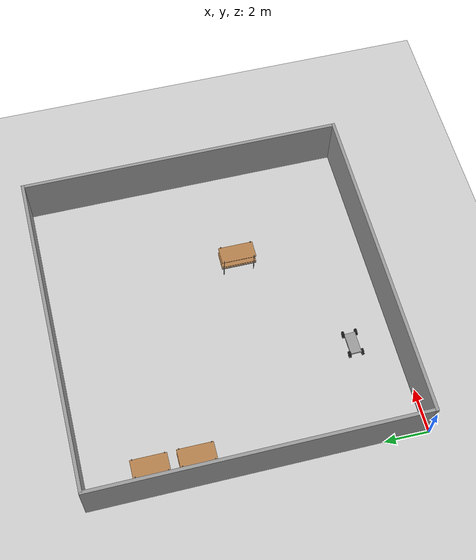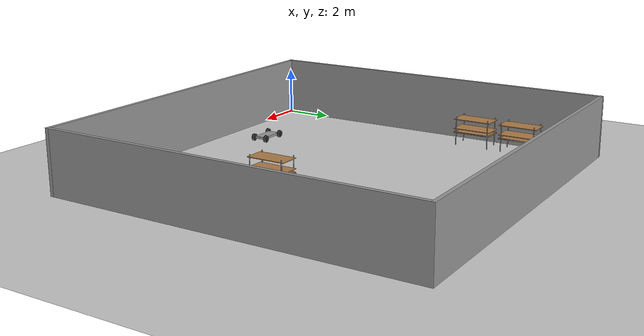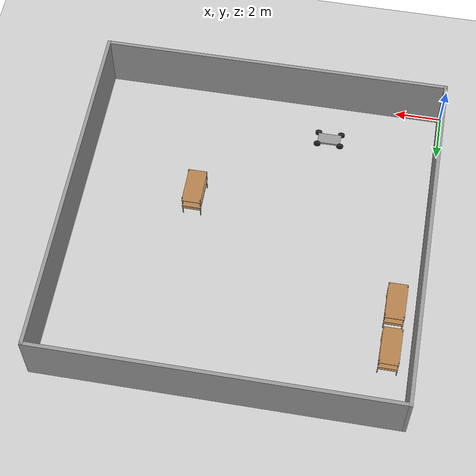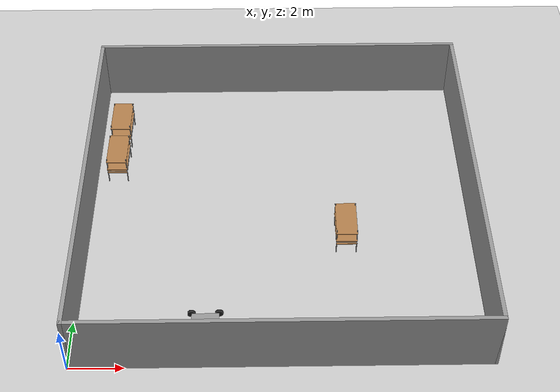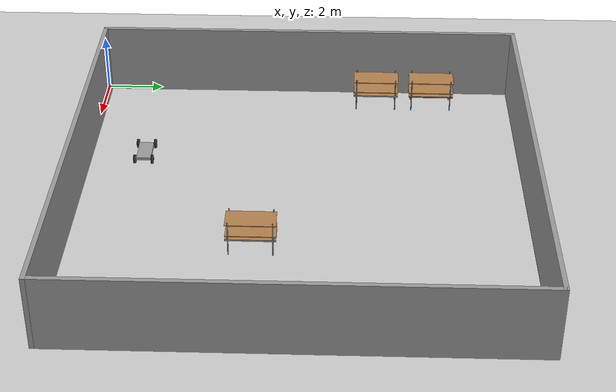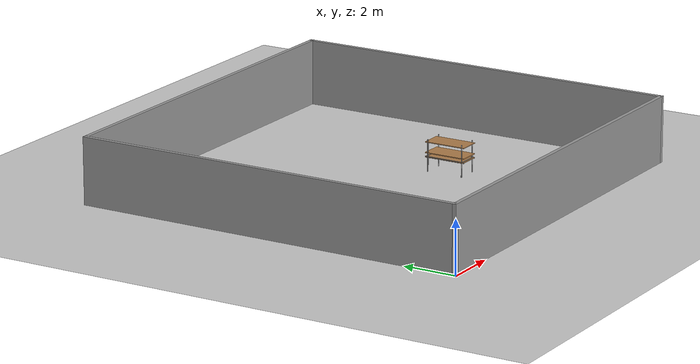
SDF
<sdf version="1.7">
 <world name="default">
  <plugin name="gazebo_ros_control" filename="libgazebo_ros_control.so"/>
  <plugin name="set_entity_state_plugin" filename="libset_entity_state.so">
   <robot_name>dynamic_obsticle</robot_name>
  </plugin>
  <light name="sun" type="directional">
   <pose>0 0 10 0 -0 0</pose>
   <diffuse>0.8 0.8 0.8 1</diffuse>
   <specular>0.2 0.2 0.2 1</specular>
   <attenuation>
    <range>1000</range>
    <constant>0.9</constant>
    <linear>0.01</linear>
    <quadratic>0.001</quadratic>
   </attenuation>
   <direction>-0.5 0.1 -0.9</direction>
   <spot><inner_angle>0</inner_angle><outer_angle>0</outer_angle><falloff>0</falloff></spot>
  </light>
  <model name="ground_plane">
   <static>1</static>
   <link name="link">
    <collision name="collision">
     <geometry><plane><normal>0 0 1</normal><size>100 100</size></plane></geometry>
     <surface><friction><ode><mu>100</mu><mu2>50</mu2></ode></friction></surface>
    </collision>
    <visual name="visual">
     <cast_shadows>0</cast_shadows>
     <geometry><plane><normal>0 0 1</normal><size>100 100</size></plane></geometry>
     <material>
      <script><uri>file://media/materials/scripts/gazebo.material</uri><name>Gazebo/Grey</name></script>
     </material>
    </visual>
   </link>
  </model>
  <gravity>0 0 -9.8</gravity>
  <magnetic_field>6e-06 2.3e-05 -4.2e-05</magnetic_field>
  <atmosphere type="adiabatic"/>
  <physics type="ode">
   <max_step_size>0.001</max_step_size>
   <real_time_factor>1</real_time_factor>
   <real_time_update_rate>1000</real_time_update_rate>
  </physics>
  <scene><ambient>0.4 0.4 0.4 1</ambient><background>0.7 0.7 0.7 1</background><shadows>1</shadows></scene>
  <audio><device>default</device></audio>
  <spherical_coordinates>
   <surface_model>EARTH_WGS84</surface_model>
   <latitude_deg>0</latitude_deg>
   <longitude_deg>0</longitude_deg>
   <elevation>0</elevation>
   <heading_deg>0</heading_deg>
  </spherical_coordinates>
  <model name="Wall">
   <pose>7.5 7.5 0 0 -0 0</pose>
   <link name="Wall_2">
    <collision name="Wall_2_Collision">
     <geometry><box><size>15 0.15 2.5</size></box></geometry>
     <pose>0 0 1.25 0 -0 0</pose>
    </collision>
    <visual name="Wall_2_Visual">
     <pose>0 0 1.25 0 -0 0</pose>
     <geometry><box><size>15 0.15 2.5</size></box></geometry>
     <material>
      <script><uri>file://media/materials/scripts/gazebo.material</uri><name>Gazebo/Grey</name></script>
      <ambient>1 1 1 1</ambient>
     </material>
     <meta><layer>0</layer></meta>
    </visual>
    <pose>-7.425 -0 0 0 -0 1.5708</pose>
   </link>
   <link name="Wall_5">
    <collision name="Wall_5_Collision">
     <geometry><box><size>15 0.15 2.5</size></box></geometry>
     <pose>0 0 1.25 0 -0 0</pose>
    </collision>
    <visual name="Wall_5_Visual">
     <pose>0 0 1.25 0 -0 0</pose>
     <geometry><box><size>15 0.15 2.5</size></box></geometry>
     <material>
      <script><uri>file://media/materials/scripts/gazebo.material</uri><name>Gazebo/Grey</name></script>
      <ambient>1 1 1 1</ambient>
     </material>
     <meta><layer>0</layer></meta>
    </visual>
    <pose>0 7.425 0 0 -0 0</pose>
   </link>
   <link name="Wall_7">
    <collision name="Wall_7_Collision">
     <geometry><box><size>15 0.15 2.5</size></box></geometry>
     <pose>0 0 1.25 0 -0 0</pose>
    </collision>
    <visual name="Wall_7_Visual">
     <pose>0 0 1.25 0 -0 0</pose>
     <geometry><box><size>15 0.15 2.5</size></box></geometry>
     <material>
      <script><uri>file://media/materials/scripts/gazebo.material</uri><name>Gazebo/Grey</name></script>
      <ambient>1 1 1 1</ambient>
     </material>
     <meta><layer>0</layer></meta>
    </visual>
    <pose>0 -7.425 0 0 -0 0</pose>
   </link>
   <link name="Wall_9">
    <collision name="Wall_9_Collision">
     <geometry><box><size>15 0.15 2.5</size></box></geometry>
     <pose>0 0 1.25 0 -0 0</pose>
    </collision>
    <visual name="Wall_9_Visual">
     <pose>0 0 1.25 0 -0 0</pose>
     <geometry><box><size>15 0.15 2.5</size></box></geometry>
     <material>
      <script><uri>file://media/materials/scripts/gazebo.material</uri><name>Gazebo/Grey</name></script>
      <ambient>1 1 1 1</ambient>
     </material>
     <meta><layer>0</layer></meta>
    </visual>
    <pose>7.425 -0 0 0 -0 -1.5708</pose>
   </link>
   <static>1</static>
  </model>
  <model name="warehouse_pallet">
   <link name="warehouse_pallet::link">
    <pose>0 0 -0 0 -0 1.57</pose>
    <inertial>
     <inertia>
      <ixx>0.0267042</ixx>
      <ixy>0</ixy>
      <ixz>0</ixz>
      <iyy>0.0937875</iyy>
      <iyz>0</iyz>
      <izz>0.120417</izz>
     </inertia>
     <mass>0.1</mass>
    </inertial>
    <visual name="holding1_visual">
     <pose>0 0.39 0.45 0 -0 0</pose>
     <geometry><box><size>1.6 0.02 0.05</size></box></geometry>
     <material>
      <script><uri>file://media/materials/scripts/gazebo.material</uri><name>Gazebo/Grey</name></script>
      <shader type="pixel"><normal_map>__default__</normal_map></shader>
      <ambient>0.3 0.3 0.3 1</ambient>
      <diffuse>0.7 0.7 0.7 1</diffuse>
      <specular>0.01 0.01 0.01 1</specular>
      <emissive>0 0 0 1</emissive>
     </material>
    </visual>
    <visual name="front_left_leg">
     <pose>0.7 0.38 0.5 0 -0 0</pose>
     <geometry><cylinder><radius>0.02</radius><length>1.2</length></cylinder></geometry>
     <material>
      <script><uri>file://media/materials/scripts/gazebo.material</uri><name>Gazebo/Grey</name></script>
      <shader type="pixel"><normal_map>__default__</normal_map></shader>
      <ambient>0.3 0.3 0.3 1</ambient>
      <diffuse>0.7 0.7 0.7 1</diffuse>
      <specular>0.01 0.01 0.01 1</specular>
      <emissive>0 0 0 1</emissive>
     </material>
    </visual>
    <visual name="front_right_leg">
     <pose>0.7 -0.38 0.5 0 -0 0</pose>
     <geometry><cylinder><radius>0.02</radius><length>1.2</length></cylinder></geometry>
     <material>
      <script><uri>file://media/materials/scripts/gazebo.material</uri><name>Gazebo/Grey</name></script>
      <shader type="pixel"><normal_map>__default__</normal_map></shader>
      <ambient>0.3 0.3 0.3 1</ambient>
      <diffuse>0.7 0.7 0.7 1</diffuse>
      <specular>0.01 0.01 0.01 1</specular>
      <emissive>0 0 0 1</emissive>
     </material>
    </visual>
    <visual name="back_right_leg">
     <pose>-0.7 -0.38 0.5 0 -0 0</pose>
     <geometry><cylinder><radius>0.02</radius><length>1.2</length></cylinder></geometry>
     <material>
      <script><uri>file://media/materials/scripts/gazebo.material</uri><name>Gazebo/Grey</name></script>
      <shader type="pixel"><normal_map>__default__</normal_map></shader>
      <ambient>0.3 0.3 0.3 1</ambient>
      <diffuse>0.7 0.7 0.7 1</diffuse>
      <specular>0.01 0.01 0.01 1</specular>
      <emissive>0 0 0 1</emissive>
     </material>
    </visual>
    <visual name="back_left_leg">
     <pose>-0.7 0.38 0.5 0 -0 0</pose>
     <geometry><cylinder><radius>0.02</radius><length>1.2</length></cylinder></geometry>
     <material>
      <script><uri>file://media/materials/scripts/gazebo.material</uri><name>Gazebo/Grey</name></script>
      <shader type="pixel"><normal_map>__default__</normal_map></shader>
      <ambient>0.3 0.3 0.3 1</ambient>
      <diffuse>0.7 0.7 0.7 1</diffuse>
      <specular>0.01 0.01 0.01 1</specular>
      <emissive>0 0 0 1</emissive>
     </material>
    </visual>
    <visual name="visual1">
     <pose>0 0 0.45 0 -0 0</pose>
     <geometry><box><size>1.6 0.8 0.03</size></box></geometry>
     <material>
      <script><uri>file://media/materials/scripts/gazebo.material</uri><name>Gazebo/Wood</name></script>
      <shader type="pixel"><normal_map>__default__</normal_map></shader>
      <ambient>1 1 1 1</ambient>
      <diffuse>1 1 1 1</diffuse>
      <specular>0.2 0.2 0.2 1</specular>
      <emissive>0 0 0 1</emissive>
     </material>
    </visual>
    <visual name="holding2_visual">
     <pose>0 -0.39 0.45 0 -0 0</pose>
     <geometry><box><size>1.6 0.02 0.05</size></box></geometry>
     <material>
      <script><uri>file://media/materials/scripts/gazebo.material</uri><name>Gazebo/Grey</name></script>
      <shader type="pixel"><normal_map>__default__</normal_map></shader>
      <ambient>0.3 0.3 0.3 1</ambient>
      <diffuse>0.7 0.7 0.7 1</diffuse>
      <specular>0.01 0.01 0.01 1</specular>
      <emissive>0 0 0 1</emissive>
     </material>
    </visual>
    <visual name="holding3_visual">
     <pose>0.735 0 0.45 0 -0 1.57</pose>
     <geometry><box><size>0.8 0.02 0.05</size></box></geometry>
     <material>
      <script><uri>file://media/materials/scripts/gazebo.material</uri><name>Gazebo/Grey</name></script>
      <shader type="pixel"><normal_map>__default__</normal_map></shader>
      <ambient>0.3 0.3 0.3 1</ambient>
      <diffuse>0.7 0.7 0.7 1</diffuse>
      <specular>0.01 0.01 0.01 1</specular>
      <emissive>0 0 0 1</emissive>
     </material>
    </visual>
    <visual name="holding4_visual">
     <pose>-0.735 0 0.45 0 -0 1.57</pose>
     <geometry><box><size>0.8 0.02 0.05</size></box></geometry>
     <material>
      <script><uri>file://media/materials/scripts/gazebo.material</uri><name>Gazebo/Grey</name></script>
      <shader type="pixel"><normal_map>__default__</normal_map></shader>
      <ambient>0.3 0.3 0.3 1</ambient>
      <diffuse>0.7 0.7 0.7 1</diffuse>
      <specular>0.01 0.01 0.01 1</specular>
      <emissive>0 0 0 1</emissive>
     </material>
    </visual>
    <visual name="visual2">
     <pose>0 0 0.6 0 -0 0</pose>
     <geometry><box><size>1.6 0.8 0.03</size></box></geometry>
     <material>
      <script><uri>file://media/materials/scripts/gazebo.material</uri><name>Gazebo/Wood</name></script>
      <shader type="pixel"><normal_map>__default__</normal_map></shader>
      <ambient>1 1 1 1</ambient>
      <diffuse>1 1 1 1</diffuse>
      <specular>0.2 0.2 0.2 1</specular>
      <emissive>0 0 0 1</emissive>
     </material>
    </visual>
    <visual name="visual3">
     <pose>0 0 1 0 -0 0</pose>
     <geometry><box><size>1.6 0.8 0.03</size></box></geometry>
     <material>
      <script><uri>file://media/materials/scripts/gazebo.material</uri><name>Gazebo/Wood</name></script>
      <shader type="pixel"><normal_map>__default__</normal_map></shader>
      <ambient>1 1 1 1</ambient>
      <diffuse>1 1 1 1</diffuse>
      <specular>0.2 0.2 0.2 1</specular>
      <emissive>0 0 0 1</emissive>
     </material>
    </visual>
    <collision name="surface1">
     <pose>0 0 0.45 0 -0 0</pose>
     <geometry><box><size>1.6 0.8 0.03</size></box></geometry>
     <surface>
      <friction>
       <ode><mu>20</mu><mu2>20</mu2><fdir1>0 0 0</fdir1><slip1>0</slip1><slip2>0</slip2></ode>
       <torsional>
        <coefficient>1</coefficient>
        <patch_radius>0</patch_radius>
        <surface_radius>0</surface_radius>
        <use_patch_radius>1</use_patch_radius>
        <ode><slip>0</slip></ode>
       </torsional>
      </friction>
      <bounce><restitution_coefficient>0</restitution_coefficient><threshold>1e+06</threshold></bounce>
      <contact>
       <collide_without_contact>0</collide_without_contact>
       <collide_without_contact_bitmask>1</collide_without_contact_bitmask>
       <collide_bitmask>1</collide_bitmask>
       <ode>
        <soft_cfm>0</soft_cfm>
        <soft_erp>0.2</soft_erp>
        <kp>1e+13</kp>
        <kd>1</kd>
        <max_vel>0.01</max_vel>
        <min_depth>0</min_depth>
       </ode>
       <bullet>
        <split_impulse>1</split_impulse>
        <split_impulse_penetration_threshold>-0.01</split_impulse_penetration_threshold>
        <soft_cfm>0</soft_cfm>
        <soft_erp>0.2</soft_erp>
        <kp>1e+13</kp>
        <kd>1</kd>
       </bullet>
      </contact>
     </surface>
    </collision>
    <collision name="holding1_collision">
     <pose>0 0.39 0.45 0 -0 0</pose>
     <geometry><box><size>1.6 0.02 0.05</size></box></geometry>
     <surface>
      <friction>
       <ode><mu>1e+09</mu><mu2>1e+09</mu2><fdir1>0 0 0</fdir1><slip1>0</slip1><slip2>0</slip2></ode>
       <torsional>
        <coefficient>1</coefficient>
        <patch_radius>0</patch_radius>
        <surface_radius>0</surface_radius>
        <use_patch_radius>1</use_patch_radius>
        <ode><slip>0</slip></ode>
       </torsional>
      </friction>
      <bounce><restitution_coefficient>0</restitution_coefficient><threshold>1e+06</threshold></bounce>
      <contact>
       <collide_without_contact>0</collide_without_contact>
       <collide_without_contact_bitmask>1</collide_without_contact_bitmask>
       <collide_bitmask>1</collide_bitmask>
       <ode>
        <soft_cfm>0</soft_cfm>
        <soft_erp>0.2</soft_erp>
        <kp>1e+13</kp>
        <kd>1</kd>
        <max_vel>0.01</max_vel>
        <min_depth>0</min_depth>
       </ode>
       <bullet>
        <split_impulse>1</split_impulse>
        <split_impulse_penetration_threshold>-0.01</split_impulse_penetration_threshold>
        <soft_cfm>0</soft_cfm>
        <soft_erp>0.2</soft_erp>
        <kp>1e+13</kp>
        <kd>1</kd>
       </bullet>
      </contact>
     </surface>
    </collision>
    <collision name="holding2_collision">
     <pose>0 -0.39 0.45 0 -0 0</pose>
     <geometry><box><size>1.6 0.02 0.05</size></box></geometry>
     <surface>
      <friction>
       <ode><mu>1e+09</mu><mu2>1e+09</mu2><fdir1>0 0 0</fdir1><slip1>0</slip1><slip2>0</slip2></ode>
       <torsional>
        <coefficient>1</coefficient>
        <patch_radius>0</patch_radius>
        <surface_radius>0</surface_radius>
        <use_patch_radius>1</use_patch_radius>
        <ode><slip>0</slip></ode>
       </torsional>
      </friction>
      <bounce><restitution_coefficient>0</restitution_coefficient><threshold>1e+06</threshold></bounce>
      <contact>
       <collide_without_contact>0</collide_without_contact>
       <collide_without_contact_bitmask>1</collide_without_contact_bitmask>
       <collide_bitmask>1</collide_bitmask>
       <ode>
        <soft_cfm>0</soft_cfm>
        <soft_erp>0.2</soft_erp>
        <kp>1e+13</kp>
        <kd>1</kd>
        <max_vel>0.01</max_vel>
        <min_depth>0</min_depth>
       </ode>
       <bullet>
        <split_impulse>1</split_impulse>
        <split_impulse_penetration_threshold>-0.01</split_impulse_penetration_threshold>
        <soft_cfm>0</soft_cfm>
        <soft_erp>0.2</soft_erp>
        <kp>1e+13</kp>
        <kd>1</kd>
       </bullet>
      </contact>
     </surface>
    </collision>
    <collision name="holding3_collision">
     <pose>0.735 0 0.45 0 -0 1.57</pose>
     <geometry><box><size>0.8 0.02 0.05</size></box></geometry>
     <surface>
      <friction>
       <ode><mu>1e+09</mu><mu2>1e+09</mu2><fdir1>0 0 0</fdir1><slip1>0</slip1><slip2>0</slip2></ode>
       <torsional>
        <coefficient>1</coefficient>
        <patch_radius>0</patch_radius>
        <surface_radius>0</surface_radius>
        <use_patch_radius>1</use_patch_radius>
        <ode><slip>0</slip></ode>
       </torsional>
      </friction>
      <bounce><restitution_coefficient>0</restitution_coefficient><threshold>1e+06</threshold></bounce>
      <contact>
       <collide_without_contact>0</collide_without_contact>
       <collide_without_contact_bitmask>1</collide_without_contact_bitmask>
       <collide_bitmask>1</collide_bitmask>
       <ode>
        <soft_cfm>0</soft_cfm>
        <soft_erp>0.2</soft_erp>
        <kp>1e+13</kp>
        <kd>1</kd>
        <max_vel>0.01</max_vel>
        <min_depth>0</min_depth>
       </ode>
       <bullet>
        <split_impulse>1</split_impulse>
        <split_impulse_penetration_threshold>-0.01</split_impulse_penetration_threshold>
        <soft_cfm>0</soft_cfm>
        <soft_erp>0.2</soft_erp>
        <kp>1e+13</kp>
        <kd>1</kd>
       </bullet>
      </contact>
     </surface>
    </collision>
    <collision name="holding4_collision">
     <pose>-0.735 0 0.45 0 -0 1.57</pose>
     <geometry><box><size>0.8 0.02 0.05</size></box></geometry>
     <surface>
      <friction>
       <ode><mu>1e+09</mu><mu2>1e+09</mu2><fdir1>0 0 0</fdir1><slip1>0</slip1><slip2>0</slip2></ode>
       <torsional>
        <coefficient>1</coefficient>
        <patch_radius>0</patch_radius>
        <surface_radius>0</surface_radius>
        <use_patch_radius>1</use_patch_radius>
        <ode><slip>0</slip></ode>
       </torsional>
      </friction>
      <bounce><restitution_coefficient>0</restitution_coefficient><threshold>1e+06</threshold></bounce>
      <contact>
       <collide_without_contact>0</collide_without_contact>
       <collide_without_contact_bitmask>1</collide_without_contact_bitmask>
       <collide_bitmask>1</collide_bitmask>
       <ode>
        <soft_cfm>0</soft_cfm>
        <soft_erp>0.2</soft_erp>
        <kp>1e+13</kp>
        <kd>1</kd>
        <max_vel>0.01</max_vel>
        <min_depth>0</min_depth>
       </ode>
       <bullet>
        <split_impulse>1</split_impulse>
        <split_impulse_penetration_threshold>-0.01</split_impulse_penetration_threshold>
        <soft_cfm>0</soft_cfm>
        <soft_erp>0.2</soft_erp>
        <kp>1e+13</kp>
        <kd>1</kd>
       </bullet>
      </contact>
     </surface>
    </collision>
    <collision name="surface3">
     <pose>0 0 1 0 -0 0</pose>
     <geometry><box><size>1.6 0.8 0.03</size></box></geometry>
     <surface>
      <friction>
       <ode><mu>2.5</mu><mu2>2.5</mu2><fdir1>0 0 0</fdir1><slip1>0</slip1><slip2>0</slip2></ode>
       <torsional>
        <coefficient>1</coefficient>
        <patch_radius>0</patch_radius>
        <surface_radius>0</surface_radius>
        <use_patch_radius>1</use_patch_radius>
        <ode><slip>0</slip></ode>
       </torsional>
      </friction>
      <bounce><restitution_coefficient>0</restitution_coefficient><threshold>1e+06</threshold></bounce>
      <contact>
       <collide_without_contact>0</collide_without_contact>
       <collide_without_contact_bitmask>1</collide_without_contact_bitmask>
       <collide_bitmask>1</collide_bitmask>
       <ode>
        <soft_cfm>0</soft_cfm>
        <soft_erp>0.2</soft_erp>
        <kp>1e+13</kp>
        <kd>1</kd>
        <max_vel>0.01</max_vel>
        <min_depth>0</min_depth>
       </ode>
       <bullet>
        <split_impulse>1</split_impulse>
        <split_impulse_penetration_threshold>-0.01</split_impulse_penetration_threshold>
        <soft_cfm>0</soft_cfm>
        <soft_erp>0.2</soft_erp>
        <kp>1e+13</kp>
        <kd>1</kd>
       </bullet>
      </contact>
     </surface>
    </collision>
    <collision name="surface2">
     <pose>0 0 0.6 0 -0 0</pose>
     <geometry><box><size>1.6 0.8 0.03</size></box></geometry>
     <surface>
      <friction>
       <ode><mu>2.5</mu><mu2>2.5</mu2><fdir1>0 0 0</fdir1><slip1>0</slip1><slip2>0</slip2></ode>
       <torsional>
        <coefficient>1</coefficient>
        <patch_radius>0</patch_radius>
        <surface_radius>0</surface_radius>
        <use_patch_radius>1</use_patch_radius>
        <ode><slip>0</slip></ode>
       </torsional>
      </friction>
      <bounce><restitution_coefficient>0</restitution_coefficient><threshold>1e+06</threshold></bounce>
      <contact>
       <collide_without_contact>0</collide_without_contact>
       <collide_without_contact_bitmask>1</collide_without_contact_bitmask>
       <collide_bitmask>1</collide_bitmask>
       <ode>
        <soft_cfm>0</soft_cfm>
        <soft_erp>0.2</soft_erp>
        <kp>1e+13</kp>
        <kd>1</kd>
        <max_vel>0.01</max_vel>
        <min_depth>0</min_depth>
       </ode>
       <bullet>
        <split_impulse>1</split_impulse>
        <split_impulse_penetration_threshold>-0.01</split_impulse_penetration_threshold>
        <soft_cfm>0</soft_cfm>
        <soft_erp>0.2</soft_erp>
        <kp>1e+13</kp>
        <kd>1</kd>
       </bullet>
      </contact>
     </surface>
    </collision>
    <collision name="front_right_leg">
     <pose>0.7 -0.38 0.5 0 -0 0</pose>
     <geometry><cylinder><radius>0.02</radius><length>1</length></cylinder></geometry>
     <surface>
      <friction>
       <ode><mu>0.1</mu><mu2>0.1</mu2><fdir1>0 0 0</fdir1><slip1>0</slip1><slip2>0</slip2></ode>
       <torsional>
        <coefficient>1</coefficient>
        <patch_radius>0</patch_radius>
        <surface_radius>0</surface_radius>
        <use_patch_radius>1</use_patch_radius>
        <ode><slip>0</slip></ode>
       </torsional>
      </friction>
      <bounce><restitution_coefficient>0</restitution_coefficient><threshold>1e+06</threshold></bounce>
      <contact>
       <collide_without_contact>0</collide_without_contact>
       <collide_without_contact_bitmask>1</collide_without_contact_bitmask>
       <collide_bitmask>1</collide_bitmask>
       <ode>
        <soft_cfm>0</soft_cfm>
        <soft_erp>0.2</soft_erp>
        <kp>1e+13</kp>
        <kd>1</kd>
        <max_vel>0.01</max_vel>
        <min_depth>0</min_depth>
       </ode>
       <bullet>
        <split_impulse>1</split_impulse>
        <split_impulse_penetration_threshold>-0.01</split_impulse_penetration_threshold>
        <soft_cfm>0</soft_cfm>
        <soft_erp>0.2</soft_erp>
        <kp>1e+13</kp>
        <kd>1</kd>
       </bullet>
      </contact>
     </surface>
    </collision>
    <collision name="back_right_leg">
     <pose>-0.7 -0.38 0.5 0 -0 0</pose>
     <geometry><cylinder><radius>0.02</radius><length>1.2</length></cylinder></geometry>
     <surface>
      <friction>
       <ode><mu>0.1</mu><mu2>0.1</mu2><fdir1>0 0 0</fdir1><slip1>0</slip1><slip2>0</slip2></ode>
       <torsional>
        <coefficient>1</coefficient>
        <patch_radius>0</patch_radius>
        <surface_radius>0</surface_radius>
        <use_patch_radius>1</use_patch_radius>
        <ode><slip>0</slip></ode>
       </torsional>
      </friction>
      <bounce><restitution_coefficient>0</restitution_coefficient><threshold>1e+06</threshold></bounce>
      <contact>
       <collide_without_contact>0</collide_without_contact>
       <collide_without_contact_bitmask>1</collide_without_contact_bitmask>
       <collide_bitmask>1</collide_bitmask>
       <ode>
        <soft_cfm>0</soft_cfm>
        <soft_erp>0.2</soft_erp>
        <kp>1e+13</kp>
        <kd>1</kd>
        <max_vel>0.01</max_vel>
        <min_depth>0</min_depth>
       </ode>
       <bullet>
        <split_impulse>1</split_impulse>
        <split_impulse_penetration_threshold>-0.01</split_impulse_penetration_threshold>
        <soft_cfm>0</soft_cfm>
        <soft_erp>0.2</soft_erp>
        <kp>1e+13</kp>
        <kd>1</kd>
       </bullet>
      </contact>
     </surface>
    </collision>
    <collision name="front_left_leg">
     <pose>0.7 0.38 0.5 0 -0 0</pose>
     <geometry><cylinder><radius>0.02</radius><length>1.2</length></cylinder></geometry>
     <surface>
      <friction>
       <ode><mu>0.1</mu><mu2>0.1</mu2><fdir1>0 0 0</fdir1><slip1>0</slip1><slip2>0</slip2></ode>
       <torsional>
        <coefficient>1</coefficient>
        <patch_radius>0</patch_radius>
        <surface_radius>0</surface_radius>
        <use_patch_radius>1</use_patch_radius>
        <ode><slip>0</slip></ode>
       </torsional>
      </friction>
      <bounce><restitution_coefficient>0</restitution_coefficient><threshold>1e+06</threshold></bounce>
      <contact>
       <collide_without_contact>0</collide_without_contact>
       <collide_without_contact_bitmask>1</collide_without_contact_bitmask>
       <collide_bitmask>1</collide_bitmask>
       <ode>
        <soft_cfm>0</soft_cfm>
        <soft_erp>0.2</soft_erp>
        <kp>1e+13</kp>
        <kd>1</kd>
        <max_vel>0.01</max_vel>
        <min_depth>0</min_depth>
       </ode>
       <bullet>
        <split_impulse>1</split_impulse>
        <split_impulse_penetration_threshold>-0.01</split_impulse_penetration_threshold>
        <soft_cfm>0</soft_cfm>
        <soft_erp>0.2</soft_erp>
        <kp>1e+13</kp>
        <kd>1</kd>
       </bullet>
      </contact>
     </surface>
    </collision>
    <collision name="back_left_leg">
     <pose>-0.7 0.38 0.5 0 -0 0</pose>
     <geometry><cylinder><radius>0.02</radius><length>1.2</length></cylinder></geometry>
     <surface>
      <friction>
       <ode><mu>0.1</mu><mu2>0.1</mu2><fdir1>0 0 0</fdir1><slip1>0</slip1><slip2>0</slip2></ode>
       <torsional>
        <coefficient>1</coefficient>
        <patch_radius>0</patch_radius>
        <surface_radius>0</surface_radius>
        <use_patch_radius>1</use_patch_radius>
        <ode><slip>0</slip></ode>
       </torsional>
      </friction>
      <bounce><restitution_coefficient>0</restitution_coefficient><threshold>1e+06</threshold></bounce>
      <contact>
       <collide_without_contact>0</collide_without_contact>
       <collide_without_contact_bitmask>1</collide_without_contact_bitmask>
       <collide_bitmask>1</collide_bitmask>
       <ode>
        <soft_cfm>0</soft_cfm>
        <soft_erp>0.2</soft_erp>
        <kp>1e+13</kp>
        <kd>1</kd>
        <max_vel>0.01</max_vel>
        <min_depth>0</min_depth>
       </ode>
       <bullet>
        <split_impulse>1</split_impulse>
        <split_impulse_penetration_threshold>-0.01</split_impulse_penetration_threshold>
        <soft_cfm>0</soft_cfm>
        <soft_erp>0.2</soft_erp>
        <kp>1e+13</kp>
        <kd>1</kd>
       </bullet>
      </contact>
     </surface>
    </collision>
   </link>
   <static>0</static>
   <pose>9.99998 5.99947 0.099998 0 7e-06 -0.004546</pose>
  </model>
  <model name="warehouse_pallet_clone">
   <link name="warehouse_pallet::link">
    <pose>0 0 -0 0 -0 1.57</pose>
    <inertial>
     <inertia>
      <ixx>0.0267042</ixx>
      <ixy>0</ixy>
      <ixz>0</ixz>
      <iyy>0.0937875</iyy>
      <iyz>0</iyz>
      <izz>0.120417</izz>
     </inertia>
     <mass>0.1</mass>
    </inertial>
    <visual name="holding1_visual">
     <pose>0 0.39 0.45 0 -0 0</pose>
     <geometry><box><size>1.6 0.02 0.05</size></box></geometry>
     <material>
      <script><uri>file://media/materials/scripts/gazebo.material</uri><name>Gazebo/Grey</name></script>
      <shader type="pixel"><normal_map>__default__</normal_map></shader>
      <ambient>0.3 0.3 0.3 1</ambient>
      <diffuse>0.7 0.7 0.7 1</diffuse>
      <specular>0.01 0.01 0.01 1</specular>
      <emissive>0 0 0 1</emissive>
     </material>
    </visual>
    <visual name="front_left_leg">
     <pose>0.7 0.38 0.5 0 -0 0</pose>
     <geometry><cylinder><radius>0.02</radius><length>1.2</length></cylinder></geometry>
     <material>
      <script><uri>file://media/materials/scripts/gazebo.material</uri><name>Gazebo/Grey</name></script>
      <shader type="pixel"><normal_map>__default__</normal_map></shader>
      <ambient>0.3 0.3 0.3 1</ambient>
      <diffuse>0.7 0.7 0.7 1</diffuse>
      <specular>0.01 0.01 0.01 1</specular>
      <emissive>0 0 0 1</emissive>
     </material>
    </visual>
    <visual name="front_right_leg">
     <pose>0.7 -0.38 0.5 0 -0 0</pose>
     <geometry><cylinder><radius>0.02</radius><length>1.2</length></cylinder></geometry>
     <material>
      <script><uri>file://media/materials/scripts/gazebo.material</uri><name>Gazebo/Grey</name></script>
      <shader type="pixel"><normal_map>__default__</normal_map></shader>
      <ambient>0.3 0.3 0.3 1</ambient>
      <diffuse>0.7 0.7 0.7 1</diffuse>
      <specular>0.01 0.01 0.01 1</specular>
      <emissive>0 0 0 1</emissive>
     </material>
    </visual>
    <visual name="back_right_leg">
     <pose>-0.7 -0.38 0.5 0 -0 0</pose>
     <geometry><cylinder><radius>0.02</radius><length>1.2</length></cylinder></geometry>
     <material>
      <script><uri>file://media/materials/scripts/gazebo.material</uri><name>Gazebo/Grey</name></script>
      <shader type="pixel"><normal_map>__default__</normal_map></shader>
      <ambient>0.3 0.3 0.3 1</ambient>
      <diffuse>0.7 0.7 0.7 1</diffuse>
      <specular>0.01 0.01 0.01 1</specular>
      <emissive>0 0 0 1</emissive>
     </material>
    </visual>
    <visual name="back_left_leg">
     <pose>-0.7 0.38 0.5 0 -0 0</pose>
     <geometry><cylinder><radius>0.02</radius><length>1.2</length></cylinder></geometry>
     <material>
      <script><uri>file://media/materials/scripts/gazebo.material</uri><name>Gazebo/Grey</name></script>
      <shader type="pixel"><normal_map>__default__</normal_map></shader>
      <ambient>0.3 0.3 0.3 1</ambient>
      <diffuse>0.7 0.7 0.7 1</diffuse>
      <specular>0.01 0.01 0.01 1</specular>
      <emissive>0 0 0 1</emissive>
     </material>
    </visual>
    <visual name="visual1">
     <pose>0 0 0.45 0 -0 0</pose>
     <geometry><box><size>1.6 0.8 0.03</size></box></geometry>
     <material>
      <script><uri>file://media/materials/scripts/gazebo.material</uri><name>Gazebo/Wood</name></script>
      <shader type="pixel"><normal_map>__default__</normal_map></shader>
      <ambient>1 1 1 1</ambient>
      <diffuse>1 1 1 1</diffuse>
      <specular>0.2 0.2 0.2 1</specular>
      <emissive>0 0 0 1</emissive>
     </material>
    </visual>
    <visual name="holding2_visual">
     <pose>0 -0.39 0.45 0 -0 0</pose>
     <geometry><box><size>1.6 0.02 0.05</size></box></geometry>
     <material>
      <script><uri>file://media/materials/scripts/gazebo.material</uri><name>Gazebo/Grey</name></script>
      <shader type="pixel"><normal_map>__default__</normal_map></shader>
      <ambient>0.3 0.3 0.3 1</ambient>
      <diffuse>0.7 0.7 0.7 1</diffuse>
      <specular>0.01 0.01 0.01 1</specular>
      <emissive>0 0 0 1</emissive>
     </material>
    </visual>
    <visual name="holding3_visual">
     <pose>0.735 0 0.45 0 -0 1.57</pose>
     <geometry><box><size>0.8 0.02 0.05</size></box></geometry>
     <material>
      <script><uri>file://media/materials/scripts/gazebo.material</uri><name>Gazebo/Grey</name></script>
      <shader type="pixel"><normal_map>__default__</normal_map></shader>
      <ambient>0.3 0.3 0.3 1</ambient>
      <diffuse>0.7 0.7 0.7 1</diffuse>
      <specular>0.01 0.01 0.01 1</specular>
      <emissive>0 0 0 1</emissive>
     </material>
    </visual>
    <visual name="holding4_visual">
     <pose>-0.735 0 0.45 0 -0 1.57</pose>
     <geometry><box><size>0.8 0.02 0.05</size></box></geometry>
     <material>
      <script><uri>file://media/materials/scripts/gazebo.material</uri><name>Gazebo/Grey</name></script>
      <shader type="pixel"><normal_map>__default__</normal_map></shader>
      <ambient>0.3 0.3 0.3 1</ambient>
      <diffuse>0.7 0.7 0.7 1</diffuse>
      <specular>0.01 0.01 0.01 1</specular>
      <emissive>0 0 0 1</emissive>
     </material>
    </visual>
    <visual name="visual2">
     <pose>0 0 0.6 0 -0 0</pose>
     <geometry><box><size>1.6 0.8 0.03</size></box></geometry>
     <material>
      <script><uri>file://media/materials/scripts/gazebo.material</uri><name>Gazebo/Wood</name></script>
      <shader type="pixel"><normal_map>__default__</normal_map></shader>
      <ambient>1 1 1 1</ambient>
      <diffuse>1 1 1 1</diffuse>
      <specular>0.2 0.2 0.2 1</specular>
      <emissive>0 0 0 1</emissive>
     </material>
    </visual>
    <visual name="visual3">
     <pose>0 0 1 0 -0 0</pose>
     <geometry><box><size>1.6 0.8 0.03</size></box></geometry>
     <material>
      <script><uri>file://media/materials/scripts/gazebo.material</uri><name>Gazebo/Wood</name></script>
      <shader type="pixel"><normal_map>__default__</normal_map></shader>
      <ambient>1 1 1 1</ambient>
      <diffuse>1 1 1 1</diffuse>
      <specular>0.2 0.2 0.2 1</specular>
      <emissive>0 0 0 1</emissive>
     </material>
    </visual>
    <collision name="surface1">
     <pose>0 0 0.45 0 -0 0</pose>
     <geometry><box><size>1.6 0.8 0.03</size></box></geometry>
     <surface>
      <friction>
       <ode><mu>20</mu><mu2>20</mu2><fdir1>0 0 0</fdir1><slip1>0</slip1><slip2>0</slip2></ode>
       <torsional>
        <coefficient>1</coefficient>
        <patch_radius>0</patch_radius>
        <surface_radius>0</surface_radius>
        <use_patch_radius>1</use_patch_radius>
        <ode><slip>0</slip></ode>
       </torsional>
      </friction>
      <bounce><restitution_coefficient>0</restitution_coefficient><threshold>1e+06</threshold></bounce>
      <contact>
       <collide_without_contact>0</collide_without_contact>
       <collide_without_contact_bitmask>1</collide_without_contact_bitmask>
       <collide_bitmask>1</collide_bitmask>
       <ode>
        <soft_cfm>0</soft_cfm>
        <soft_erp>0.2</soft_erp>
        <kp>1e+13</kp>
        <kd>1</kd>
        <max_vel>0.01</max_vel>
        <min_depth>0</min_depth>
       </ode>
       <bullet>
        <split_impulse>1</split_impulse>
        <split_impulse_penetration_threshold>-0.01</split_impulse_penetration_threshold>
        <soft_cfm>0</soft_cfm>
        <soft_erp>0.2</soft_erp>
        <kp>1e+13</kp>
        <kd>1</kd>
       </bullet>
      </contact>
     </surface>
    </collision>
    <collision name="holding1_collision">
     <pose>0 0.39 0.45 0 -0 0</pose>
     <geometry><box><size>1.6 0.02 0.05</size></box></geometry>
     <surface>
      <friction>
       <ode><mu>1e+09</mu><mu2>1e+09</mu2><fdir1>0 0 0</fdir1><slip1>0</slip1><slip2>0</slip2></ode>
       <torsional>
        <coefficient>1</coefficient>
        <patch_radius>0</patch_radius>
        <surface_radius>0</surface_radius>
        <use_patch_radius>1</use_patch_radius>
        <ode><slip>0</slip></ode>
       </torsional>
      </friction>
      <bounce><restitution_coefficient>0</restitution_coefficient><threshold>1e+06</threshold></bounce>
      <contact>
       <collide_without_contact>0</collide_without_contact>
       <collide_without_contact_bitmask>1</collide_without_contact_bitmask>
       <collide_bitmask>1</collide_bitmask>
       <ode>
        <soft_cfm>0</soft_cfm>
        <soft_erp>0.2</soft_erp>
        <kp>1e+13</kp>
        <kd>1</kd>
        <max_vel>0.01</max_vel>
        <min_depth>0</min_depth>
       </ode>
       <bullet>
        <split_impulse>1</split_impulse>
        <split_impulse_penetration_threshold>-0.01</split_impulse_penetration_threshold>
        <soft_cfm>0</soft_cfm>
        <soft_erp>0.2</soft_erp>
        <kp>1e+13</kp>
        <kd>1</kd>
       </bullet>
      </contact>
     </surface>
    </collision>
    <collision name="holding2_collision">
     <pose>0 -0.39 0.45 0 -0 0</pose>
     <geometry><box><size>1.6 0.02 0.05</size></box></geometry>
     <surface>
      <friction>
       <ode><mu>1e+09</mu><mu2>1e+09</mu2><fdir1>0 0 0</fdir1><slip1>0</slip1><slip2>0</slip2></ode>
       <torsional>
        <coefficient>1</coefficient>
        <patch_radius>0</patch_radius>
        <surface_radius>0</surface_radius>
        <use_patch_radius>1</use_patch_radius>
        <ode><slip>0</slip></ode>
       </torsional>
      </friction>
      <bounce><restitution_coefficient>0</restitution_coefficient><threshold>1e+06</threshold></bounce>
      <contact>
       <collide_without_contact>0</collide_without_contact>
       <collide_without_contact_bitmask>1</collide_without_contact_bitmask>
       <collide_bitmask>1</collide_bitmask>
       <ode>
        <soft_cfm>0</soft_cfm>
        <soft_erp>0.2</soft_erp>
        <kp>1e+13</kp>
        <kd>1</kd>
        <max_vel>0.01</max_vel>
        <min_depth>0</min_depth>
       </ode>
       <bullet>
        <split_impulse>1</split_impulse>
        <split_impulse_penetration_threshold>-0.01</split_impulse_penetration_threshold>
        <soft_cfm>0</soft_cfm>
        <soft_erp>0.2</soft_erp>
        <kp>1e+13</kp>
        <kd>1</kd>
       </bullet>
      </contact>
     </surface>
    </collision>
    <collision name="holding3_collision">
     <pose>0.735 0 0.45 0 -0 1.57</pose>
     <geometry><box><size>0.8 0.02 0.05</size></box></geometry>
     <surface>
      <friction>
       <ode><mu>1e+09</mu><mu2>1e+09</mu2><fdir1>0 0 0</fdir1><slip1>0</slip1><slip2>0</slip2></ode>
       <torsional>
        <coefficient>1</coefficient>
        <patch_radius>0</patch_radius>
        <surface_radius>0</surface_radius>
        <use_patch_radius>1</use_patch_radius>
        <ode><slip>0</slip></ode>
       </torsional>
      </friction>
      <bounce><restitution_coefficient>0</restitution_coefficient><threshold>1e+06</threshold></bounce>
      <contact>
       <collide_without_contact>0</collide_without_contact>
       <collide_without_contact_bitmask>1</collide_without_contact_bitmask>
       <collide_bitmask>1</collide_bitmask>
       <ode>
        <soft_cfm>0</soft_cfm>
        <soft_erp>0.2</soft_erp>
        <kp>1e+13</kp>
        <kd>1</kd>
        <max_vel>0.01</max_vel>
        <min_depth>0</min_depth>
       </ode>
       <bullet>
        <split_impulse>1</split_impulse>
        <split_impulse_penetration_threshold>-0.01</split_impulse_penetration_threshold>
        <soft_cfm>0</soft_cfm>
        <soft_erp>0.2</soft_erp>
        <kp>1e+13</kp>
        <kd>1</kd>
       </bullet>
      </contact>
     </surface>
    </collision>
    <collision name="holding4_collision">
     <pose>-0.735 0 0.45 0 -0 1.57</pose>
     <geometry><box><size>0.8 0.02 0.05</size></box></geometry>
     <surface>
      <friction>
       <ode><mu>1e+09</mu><mu2>1e+09</mu2><fdir1>0 0 0</fdir1><slip1>0</slip1><slip2>0</slip2></ode>
       <torsional>
        <coefficient>1</coefficient>
        <patch_radius>0</patch_radius>
        <surface_radius>0</surface_radius>
        <use_patch_radius>1</use_patch_radius>
        <ode><slip>0</slip></ode>
       </torsional>
      </friction>
      <bounce><restitution_coefficient>0</restitution_coefficient><threshold>1e+06</threshold></bounce>
      <contact>
       <collide_without_contact>0</collide_without_contact>
       <collide_without_contact_bitmask>1</collide_without_contact_bitmask>
       <collide_bitmask>1</collide_bitmask>
       <ode>
        <soft_cfm>0</soft_cfm>
        <soft_erp>0.2</soft_erp>
        <kp>1e+13</kp>
        <kd>1</kd>
        <max_vel>0.01</max_vel>
        <min_depth>0</min_depth>
       </ode>
       <bullet>
        <split_impulse>1</split_impulse>
        <split_impulse_penetration_threshold>-0.01</split_impulse_penetration_threshold>
        <soft_cfm>0</soft_cfm>
        <soft_erp>0.2</soft_erp>
        <kp>1e+13</kp>
        <kd>1</kd>
       </bullet>
      </contact>
     </surface>
    </collision>
    <collision name="surface3">
     <pose>0 0 1 0 -0 0</pose>
     <geometry><box><size>1.6 0.8 0.03</size></box></geometry>
     <surface>
      <friction>
       <ode><mu>2.5</mu><mu2>2.5</mu2><fdir1>0 0 0</fdir1><slip1>0</slip1><slip2>0</slip2></ode>
       <torsional>
        <coefficient>1</coefficient>
        <patch_radius>0</patch_radius>
        <surface_radius>0</surface_radius>
        <use_patch_radius>1</use_patch_radius>
        <ode><slip>0</slip></ode>
       </torsional>
      </friction>
      <bounce><restitution_coefficient>0</restitution_coefficient><threshold>1e+06</threshold></bounce>
      <contact>
       <collide_without_contact>0</collide_without_contact>
       <collide_without_contact_bitmask>1</collide_without_contact_bitmask>
       <collide_bitmask>1</collide_bitmask>
       <ode>
        <soft_cfm>0</soft_cfm>
        <soft_erp>0.2</soft_erp>
        <kp>1e+13</kp>
        <kd>1</kd>
        <max_vel>0.01</max_vel>
        <min_depth>0</min_depth>
       </ode>
       <bullet>
        <split_impulse>1</split_impulse>
        <split_impulse_penetration_threshold>-0.01</split_impulse_penetration_threshold>
        <soft_cfm>0</soft_cfm>
        <soft_erp>0.2</soft_erp>
        <kp>1e+13</kp>
        <kd>1</kd>
       </bullet>
      </contact>
     </surface>
    </collision>
    <collision name="surface2">
     <pose>0 0 0.6 0 -0 0</pose>
     <geometry><box><size>1.6 0.8 0.03</size></box></geometry>
     <surface>
      <friction>
       <ode><mu>2.5</mu><mu2>2.5</mu2><fdir1>0 0 0</fdir1><slip1>0</slip1><slip2>0</slip2></ode>
       <torsional>
        <coefficient>1</coefficient>
        <patch_radius>0</patch_radius>
        <surface_radius>0</surface_radius>
        <use_patch_radius>1</use_patch_radius>
        <ode><slip>0</slip></ode>
       </torsional>
      </friction>
      <bounce><restitution_coefficient>0</restitution_coefficient><threshold>1e+06</threshold></bounce>
      <contact>
       <collide_without_contact>0</collide_without_contact>
       <collide_without_contact_bitmask>1</collide_without_contact_bitmask>
       <collide_bitmask>1</collide_bitmask>
       <ode>
        <soft_cfm>0</soft_cfm>
        <soft_erp>0.2</soft_erp>
        <kp>1e+13</kp>
        <kd>1</kd>
        <max_vel>0.01</max_vel>
        <min_depth>0</min_depth>
       </ode>
       <bullet>
        <split_impulse>1</split_impulse>
        <split_impulse_penetration_threshold>-0.01</split_impulse_penetration_threshold>
        <soft_cfm>0</soft_cfm>
        <soft_erp>0.2</soft_erp>
        <kp>1e+13</kp>
        <kd>1</kd>
       </bullet>
      </contact>
     </surface>
    </collision>
    <collision name="front_right_leg">
     <pose>0.7 -0.38 0.5 0 -0 0</pose>
     <geometry><cylinder><radius>0.02</radius><length>1</length></cylinder></geometry>
     <surface>
      <friction>
       <ode><mu>0.1</mu><mu2>0.1</mu2><fdir1>0 0 0</fdir1><slip1>0</slip1><slip2>0</slip2></ode>
       <torsional>
        <coefficient>1</coefficient>
        <patch_radius>0</patch_radius>
        <surface_radius>0</surface_radius>
        <use_patch_radius>1</use_patch_radius>
        <ode><slip>0</slip></ode>
       </torsional>
      </friction>
      <bounce><restitution_coefficient>0</restitution_coefficient><threshold>1e+06</threshold></bounce>
      <contact>
       <collide_without_contact>0</collide_without_contact>
       <collide_without_contact_bitmask>1</collide_without_contact_bitmask>
       <collide_bitmask>1</collide_bitmask>
       <ode>
        <soft_cfm>0</soft_cfm>
        <soft_erp>0.2</soft_erp>
        <kp>1e+13</kp>
        <kd>1</kd>
        <max_vel>0.01</max_vel>
        <min_depth>0</min_depth>
       </ode>
       <bullet>
        <split_impulse>1</split_impulse>
        <split_impulse_penetration_threshold>-0.01</split_impulse_penetration_threshold>
        <soft_cfm>0</soft_cfm>
        <soft_erp>0.2</soft_erp>
        <kp>1e+13</kp>
        <kd>1</kd>
       </bullet>
      </contact>
     </surface>
    </collision>
    <collision name="back_right_leg">
     <pose>-0.7 -0.38 0.5 0 -0 0</pose>
     <geometry><cylinder><radius>0.02</radius><length>1.2</length></cylinder></geometry>
     <surface>
      <friction>
       <ode><mu>0.1</mu><mu2>0.1</mu2><fdir1>0 0 0</fdir1><slip1>0</slip1><slip2>0</slip2></ode>
       <torsional>
        <coefficient>1</coefficient>
        <patch_radius>0</patch_radius>
        <surface_radius>0</surface_radius>
        <use_patch_radius>1</use_patch_radius>
        <ode><slip>0</slip></ode>
       </torsional>
      </friction>
      <bounce><restitution_coefficient>0</restitution_coefficient><threshold>1e+06</threshold></bounce>
      <contact>
       <collide_without_contact>0</collide_without_contact>
       <collide_without_contact_bitmask>1</collide_without_contact_bitmask>
       <collide_bitmask>1</collide_bitmask>
       <ode>
        <soft_cfm>0</soft_cfm>
        <soft_erp>0.2</soft_erp>
        <kp>1e+13</kp>
        <kd>1</kd>
        <max_vel>0.01</max_vel>
        <min_depth>0</min_depth>
       </ode>
       <bullet>
        <split_impulse>1</split_impulse>
        <split_impulse_penetration_threshold>-0.01</split_impulse_penetration_threshold>
        <soft_cfm>0</soft_cfm>
        <soft_erp>0.2</soft_erp>
        <kp>1e+13</kp>
        <kd>1</kd>
       </bullet>
      </contact>
     </surface>
    </collision>
    <collision name="front_left_leg">
     <pose>0.7 0.38 0.5 0 -0 0</pose>
     <geometry><cylinder><radius>0.02</radius><length>1.2</length></cylinder></geometry>
     <surface>
      <friction>
       <ode><mu>0.1</mu><mu2>0.1</mu2><fdir1>0 0 0</fdir1><slip1>0</slip1><slip2>0</slip2></ode>
       <torsional>
        <coefficient>1</coefficient>
        <patch_radius>0</patch_radius>
        <surface_radius>0</surface_radius>
        <use_patch_radius>1</use_patch_radius>
        <ode><slip>0</slip></ode>
       </torsional>
      </friction>
      <bounce><restitution_coefficient>0</restitution_coefficient><threshold>1e+06</threshold></bounce>
      <contact>
       <collide_without_contact>0</collide_without_contact>
       <collide_without_contact_bitmask>1</collide_without_contact_bitmask>
       <collide_bitmask>1</collide_bitmask>
       <ode>
        <soft_cfm>0</soft_cfm>
        <soft_erp>0.2</soft_erp>
        <kp>1e+13</kp>
        <kd>1</kd>
        <max_vel>0.01</max_vel>
        <min_depth>0</min_depth>
       </ode>
       <bullet>
        <split_impulse>1</split_impulse>
        <split_impulse_penetration_threshold>-0.01</split_impulse_penetration_threshold>
        <soft_cfm>0</soft_cfm>
        <soft_erp>0.2</soft_erp>
        <kp>1e+13</kp>
        <kd>1</kd>
       </bullet>
      </contact>
     </surface>
    </collision>
    <collision name="back_left_leg">
     <pose>-0.7 0.38 0.5 0 -0 0</pose>
     <geometry><cylinder><radius>0.02</radius><length>1.2</length></cylinder></geometry>
     <surface>
      <friction>
       <ode><mu>0.1</mu><mu2>0.1</mu2><fdir1>0 0 0</fdir1><slip1>0</slip1><slip2>0</slip2></ode>
       <torsional>
        <coefficient>1</coefficient>
        <patch_radius>0</patch_radius>
        <surface_radius>0</surface_radius>
        <use_patch_radius>1</use_patch_radius>
        <ode><slip>0</slip></ode>
       </torsional>
      </friction>
      <bounce><restitution_coefficient>0</restitution_coefficient><threshold>1e+06</threshold></bounce>
      <contact>
       <collide_without_contact>0</collide_without_contact>
       <collide_without_contact_bitmask>1</collide_without_contact_bitmask>
       <collide_bitmask>1</collide_bitmask>
       <ode>
        <soft_cfm>0</soft_cfm>
        <soft_erp>0.2</soft_erp>
        <kp>1e+13</kp>
        <kd>1</kd>
        <max_vel>0.01</max_vel>
        <min_depth>0</min_depth>
       </ode>
       <bullet>
        <split_impulse>1</split_impulse>
        <split_impulse_penetration_threshold>-0.01</split_impulse_penetration_threshold>
        <soft_cfm>0</soft_cfm>
        <soft_erp>0.2</soft_erp>
        <kp>1e+13</kp>
        <kd>1</kd>
       </bullet>
      </contact>
     </surface>
    </collision>
   </link>
   <static>0</static>
   <pose>0.99998 11.9995 0.099998 0 7e-06 -0.00454</pose>
  </model>
  <model name="warehouse_pallet_clone_clone">
   <link name="warehouse_pallet::link">
    <pose>0 0 -0 0 -0 1.57</pose>
    <inertial>
     <inertia>
      <ixx>0.0267042</ixx>
      <ixy>0</ixy>
      <ixz>0</ixz>
      <iyy>0.0937875</iyy>
      <iyz>0</iyz>
      <izz>0.120417</izz>
     </inertia>
     <mass>0.1</mass>
    </inertial>
    <visual name="holding1_visual">
     <pose>0 0.39 0.45 0 -0 0</pose>
     <geometry><box><size>1.6 0.02 0.05</size></box></geometry>
     <material>
      <script><uri>file://media/materials/scripts/gazebo.material</uri><name>Gazebo/Grey</name></script>
      <shader type="pixel"><normal_map>__default__</normal_map></shader>
      <ambient>0.3 0.3 0.3 1</ambient>
      <diffuse>0.7 0.7 0.7 1</diffuse>
      <specular>0.01 0.01 0.01 1</specular>
      <emissive>0 0 0 1</emissive>
     </material>
    </visual>
    <visual name="front_left_leg">
     <pose>0.7 0.38 0.5 0 -0 0</pose>
     <geometry><cylinder><radius>0.02</radius><length>1.2</length></cylinder></geometry>
     <material>
      <script><uri>file://media/materials/scripts/gazebo.material</uri><name>Gazebo/Grey</name></script>
      <shader type="pixel"><normal_map>__default__</normal_map></shader>
      <ambient>0.3 0.3 0.3 1</ambient>
      <diffuse>0.7 0.7 0.7 1</diffuse>
      <specular>0.01 0.01 0.01 1</specular>
      <emissive>0 0 0 1</emissive>
     </material>
    </visual>
    <visual name="front_right_leg">
     <pose>0.7 -0.38 0.5 0 -0 0</pose>
     <geometry><cylinder><radius>0.02</radius><length>1.2</length></cylinder></geometry>
     <material>
      <script><uri>file://media/materials/scripts/gazebo.material</uri><name>Gazebo/Grey</name></script>
      <shader type="pixel"><normal_map>__default__</normal_map></shader>
      <ambient>0.3 0.3 0.3 1</ambient>
      <diffuse>0.7 0.7 0.7 1</diffuse>
      <specular>0.01 0.01 0.01 1</specular>
      <emissive>0 0 0 1</emissive>
     </material>
    </visual>
    <visual name="back_right_leg">
     <pose>-0.7 -0.38 0.5 0 -0 0</pose>
     <geometry><cylinder><radius>0.02</radius><length>1.2</length></cylinder></geometry>
     <material>
      <script><uri>file://media/materials/scripts/gazebo.material</uri><name>Gazebo/Grey</name></script>
      <shader type="pixel"><normal_map>__default__</normal_map></shader>
      <ambient>0.3 0.3 0.3 1</ambient>
      <diffuse>0.7 0.7 0.7 1</diffuse>
      <specular>0.01 0.01 0.01 1</specular>
      <emissive>0 0 0 1</emissive>
     </material>
    </visual>
    <visual name="back_left_leg">
     <pose>-0.7 0.38 0.5 0 -0 0</pose>
     <geometry><cylinder><radius>0.02</radius><length>1.2</length></cylinder></geometry>
     <material>
      <script><uri>file://media/materials/scripts/gazebo.material</uri><name>Gazebo/Grey</name></script>
      <shader type="pixel"><normal_map>__default__</normal_map></shader>
      <ambient>0.3 0.3 0.3 1</ambient>
      <diffuse>0.7 0.7 0.7 1</diffuse>
      <specular>0.01 0.01 0.01 1</specular>
      <emissive>0 0 0 1</emissive>
     </material>
    </visual>
    <visual name="visual1">
     <pose>0 0 0.45 0 -0 0</pose>
     <geometry><box><size>1.6 0.8 0.03</size></box></geometry>
     <material>
      <script><uri>file://media/materials/scripts/gazebo.material</uri><name>Gazebo/Wood</name></script>
      <shader type="pixel"><normal_map>__default__</normal_map></shader>
      <ambient>1 1 1 1</ambient>
      <diffuse>1 1 1 1</diffuse>
      <specular>0.2 0.2 0.2 1</specular>
      <emissive>0 0 0 1</emissive>
     </material>
    </visual>
    <visual name="holding2_visual">
     <pose>0 -0.39 0.45 0 -0 0</pose>
     <geometry><box><size>1.6 0.02 0.05</size></box></geometry>
     <material>
      <script><uri>file://media/materials/scripts/gazebo.material</uri><name>Gazebo/Grey</name></script>
      <shader type="pixel"><normal_map>__default__</normal_map></shader>
      <ambient>0.3 0.3 0.3 1</ambient>
      <diffuse>0.7 0.7 0.7 1</diffuse>
      <specular>0.01 0.01 0.01 1</specular>
      <emissive>0 0 0 1</emissive>
     </material>
    </visual>
    <visual name="holding3_visual">
     <pose>0.735 0 0.45 0 -0 1.57</pose>
     <geometry><box><size>0.8 0.02 0.05</size></box></geometry>
     <material>
      <script><uri>file://media/materials/scripts/gazebo.material</uri><name>Gazebo/Grey</name></script>
      <shader type="pixel"><normal_map>__default__</normal_map></shader>
      <ambient>0.3 0.3 0.3 1</ambient>
      <diffuse>0.7 0.7 0.7 1</diffuse>
      <specular>0.01 0.01 0.01 1</specular>
      <emissive>0 0 0 1</emissive>
     </material>
    </visual>
    <visual name="holding4_visual">
     <pose>-0.735 0 0.45 0 -0 1.57</pose>
     <geometry><box><size>0.8 0.02 0.05</size></box></geometry>
     <material>
      <script><uri>file://media/materials/scripts/gazebo.material</uri><name>Gazebo/Grey</name></script>
      <shader type="pixel"><normal_map>__default__</normal_map></shader>
      <ambient>0.3 0.3 0.3 1</ambient>
      <diffuse>0.7 0.7 0.7 1</diffuse>
      <specular>0.01 0.01 0.01 1</specular>
      <emissive>0 0 0 1</emissive>
     </material>
    </visual>
    <visual name="visual2">
     <pose>0 0 0.6 0 -0 0</pose>
     <geometry><box><size>1.6 0.8 0.03</size></box></geometry>
     <material>
      <script><uri>file://media/materials/scripts/gazebo.material</uri><name>Gazebo/Wood</name></script>
      <shader type="pixel"><normal_map>__default__</normal_map></shader>
      <ambient>1 1 1 1</ambient>
      <diffuse>1 1 1 1</diffuse>
      <specular>0.2 0.2 0.2 1</specular>
      <emissive>0 0 0 1</emissive>
     </material>
    </visual>
    <visual name="visual3">
     <pose>0 0 1 0 -0 0</pose>
     <geometry><box><size>1.6 0.8 0.03</size></box></geometry>
     <material>
      <script><uri>file://media/materials/scripts/gazebo.material</uri><name>Gazebo/Wood</name></script>
      <shader type="pixel"><normal_map>__default__</normal_map></shader>
      <ambient>1 1 1 1</ambient>
      <diffuse>1 1 1 1</diffuse>
      <specular>0.2 0.2 0.2 1</specular>
      <emissive>0 0 0 1</emissive>
     </material>
    </visual>
    <collision name="surface1">
     <pose>0 0 0.45 0 -0 0</pose>
     <geometry><box><size>1.6 0.8 0.03</size></box></geometry>
     <surface>
      <friction>
       <ode><mu>20</mu><mu2>20</mu2><fdir1>0 0 0</fdir1><slip1>0</slip1><slip2>0</slip2></ode>
       <torsional>
        <coefficient>1</coefficient>
        <patch_radius>0</patch_radius>
        <surface_radius>0</surface_radius>
        <use_patch_radius>1</use_patch_radius>
        <ode><slip>0</slip></ode>
       </torsional>
      </friction>
      <bounce><restitution_coefficient>0</restitution_coefficient><threshold>1e+06</threshold></bounce>
      <contact>
       <collide_without_contact>0</collide_without_contact>
       <collide_without_contact_bitmask>1</collide_without_contact_bitmask>
       <collide_bitmask>1</collide_bitmask>
       <ode>
        <soft_cfm>0</soft_cfm>
        <soft_erp>0.2</soft_erp>
        <kp>1e+13</kp>
        <kd>1</kd>
        <max_vel>0.01</max_vel>
        <min_depth>0</min_depth>
       </ode>
       <bullet>
        <split_impulse>1</split_impulse>
        <split_impulse_penetration_threshold>-0.01</split_impulse_penetration_threshold>
        <soft_cfm>0</soft_cfm>
        <soft_erp>0.2</soft_erp>
        <kp>1e+13</kp>
        <kd>1</kd>
       </bullet>
      </contact>
     </surface>
    </collision>
    <collision name="holding1_collision">
     <pose>0 0.39 0.45 0 -0 0</pose>
     <geometry><box><size>1.6 0.02 0.05</size></box></geometry>
     <surface>
      <friction>
       <ode><mu>1e+09</mu><mu2>1e+09</mu2><fdir1>0 0 0</fdir1><slip1>0</slip1><slip2>0</slip2></ode>
       <torsional>
        <coefficient>1</coefficient>
        <patch_radius>0</patch_radius>
        <surface_radius>0</surface_radius>
        <use_patch_radius>1</use_patch_radius>
        <ode><slip>0</slip></ode>
       </torsional>
      </friction>
      <bounce><restitution_coefficient>0</restitution_coefficient><threshold>1e+06</threshold></bounce>
      <contact>
       <collide_without_contact>0</collide_without_contact>
       <collide_without_contact_bitmask>1</collide_without_contact_bitmask>
       <collide_bitmask>1</collide_bitmask>
       <ode>
        <soft_cfm>0</soft_cfm>
        <soft_erp>0.2</soft_erp>
        <kp>1e+13</kp>
        <kd>1</kd>
        <max_vel>0.01</max_vel>
        <min_depth>0</min_depth>
       </ode>
       <bullet>
        <split_impulse>1</split_impulse>
        <split_impulse_penetration_threshold>-0.01</split_impulse_penetration_threshold>
        <soft_cfm>0</soft_cfm>
        <soft_erp>0.2</soft_erp>
        <kp>1e+13</kp>
        <kd>1</kd>
       </bullet>
      </contact>
     </surface>
    </collision>
    <collision name="holding2_collision">
     <pose>0 -0.39 0.45 0 -0 0</pose>
     <geometry><box><size>1.6 0.02 0.05</size></box></geometry>
     <surface>
      <friction>
       <ode><mu>1e+09</mu><mu2>1e+09</mu2><fdir1>0 0 0</fdir1><slip1>0</slip1><slip2>0</slip2></ode>
       <torsional>
        <coefficient>1</coefficient>
        <patch_radius>0</patch_radius>
        <surface_radius>0</surface_radius>
        <use_patch_radius>1</use_patch_radius>
        <ode><slip>0</slip></ode>
       </torsional>
      </friction>
      <bounce><restitution_coefficient>0</restitution_coefficient><threshold>1e+06</threshold></bounce>
      <contact>
       <collide_without_contact>0</collide_without_contact>
       <collide_without_contact_bitmask>1</collide_without_contact_bitmask>
       <collide_bitmask>1</collide_bitmask>
       <ode>
        <soft_cfm>0</soft_cfm>
        <soft_erp>0.2</soft_erp>
        <kp>1e+13</kp>
        <kd>1</kd>
        <max_vel>0.01</max_vel>
        <min_depth>0</min_depth>
       </ode>
       <bullet>
        <split_impulse>1</split_impulse>
        <split_impulse_penetration_threshold>-0.01</split_impulse_penetration_threshold>
        <soft_cfm>0</soft_cfm>
        <soft_erp>0.2</soft_erp>
        <kp>1e+13</kp>
        <kd>1</kd>
       </bullet>
      </contact>
     </surface>
    </collision>
    <collision name="holding3_collision">
     <pose>0.735 0 0.45 0 -0 1.57</pose>
     <geometry><box><size>0.8 0.02 0.05</size></box></geometry>
     <surface>
      <friction>
       <ode><mu>1e+09</mu><mu2>1e+09</mu2><fdir1>0 0 0</fdir1><slip1>0</slip1><slip2>0</slip2></ode>
       <torsional>
        <coefficient>1</coefficient>
        <patch_radius>0</patch_radius>
        <surface_radius>0</surface_radius>
        <use_patch_radius>1</use_patch_radius>
        <ode><slip>0</slip></ode>
       </torsional>
      </friction>
      <bounce><restitution_coefficient>0</restitution_coefficient><threshold>1e+06</threshold></bounce>
      <contact>
       <collide_without_contact>0</collide_without_contact>
       <collide_without_contact_bitmask>1</collide_without_contact_bitmask>
       <collide_bitmask>1</collide_bitmask>
       <ode>
        <soft_cfm>0</soft_cfm>
        <soft_erp>0.2</soft_erp>
        <kp>1e+13</kp>
        <kd>1</kd>
        <max_vel>0.01</max_vel>
        <min_depth>0</min_depth>
       </ode>
       <bullet>
        <split_impulse>1</split_impulse>
        <split_impulse_penetration_threshold>-0.01</split_impulse_penetration_threshold>
        <soft_cfm>0</soft_cfm>
        <soft_erp>0.2</soft_erp>
        <kp>1e+13</kp>
        <kd>1</kd>
       </bullet>
      </contact>
     </surface>
    </collision>
    <collision name="holding4_collision">
     <pose>-0.735 0 0.45 0 -0 1.57</pose>
     <geometry><box><size>0.8 0.02 0.05</size></box></geometry>
     <surface>
      <friction>
       <ode><mu>1e+09</mu><mu2>1e+09</mu2><fdir1>0 0 0</fdir1><slip1>0</slip1><slip2>0</slip2></ode>
       <torsional>
        <coefficient>1</coefficient>
        <patch_radius>0</patch_radius>
        <surface_radius>0</surface_radius>
        <use_patch_radius>1</use_patch_radius>
        <ode><slip>0</slip></ode>
       </torsional>
      </friction>
      <bounce><restitution_coefficient>0</restitution_coefficient><threshold>1e+06</threshold></bounce>
      <contact>
       <collide_without_contact>0</collide_without_contact>
       <collide_without_contact_bitmask>1</collide_without_contact_bitmask>
       <collide_bitmask>1</collide_bitmask>
       <ode>
        <soft_cfm>0</soft_cfm>
        <soft_erp>0.2</soft_erp>
        <kp>1e+13</kp>
        <kd>1</kd>
        <max_vel>0.01</max_vel>
        <min_depth>0</min_depth>
       </ode>
       <bullet>
        <split_impulse>1</split_impulse>
        <split_impulse_penetration_threshold>-0.01</split_impulse_penetration_threshold>
        <soft_cfm>0</soft_cfm>
        <soft_erp>0.2</soft_erp>
        <kp>1e+13</kp>
        <kd>1</kd>
       </bullet>
      </contact>
     </surface>
    </collision>
    <collision name="surface3">
     <pose>0 0 1 0 -0 0</pose>
     <geometry><box><size>1.6 0.8 0.03</size></box></geometry>
     <surface>
      <friction>
       <ode><mu>2.5</mu><mu2>2.5</mu2><fdir1>0 0 0</fdir1><slip1>0</slip1><slip2>0</slip2></ode>
       <torsional>
        <coefficient>1</coefficient>
        <patch_radius>0</patch_radius>
        <surface_radius>0</surface_radius>
        <use_patch_radius>1</use_patch_radius>
        <ode><slip>0</slip></ode>
       </torsional>
      </friction>
      <bounce><restitution_coefficient>0</restitution_coefficient><threshold>1e+06</threshold></bounce>
      <contact>
       <collide_without_contact>0</collide_without_contact>
       <collide_without_contact_bitmask>1</collide_without_contact_bitmask>
       <collide_bitmask>1</collide_bitmask>
       <ode>
        <soft_cfm>0</soft_cfm>
        <soft_erp>0.2</soft_erp>
        <kp>1e+13</kp>
        <kd>1</kd>
        <max_vel>0.01</max_vel>
        <min_depth>0</min_depth>
       </ode>
       <bullet>
        <split_impulse>1</split_impulse>
        <split_impulse_penetration_threshold>-0.01</split_impulse_penetration_threshold>
        <soft_cfm>0</soft_cfm>
        <soft_erp>0.2</soft_erp>
        <kp>1e+13</kp>
        <kd>1</kd>
       </bullet>
      </contact>
     </surface>
    </collision>
    <collision name="surface2">
     <pose>0 0 0.6 0 -0 0</pose>
     <geometry><box><size>1.6 0.8 0.03</size></box></geometry>
     <surface>
      <friction>
       <ode><mu>2.5</mu><mu2>2.5</mu2><fdir1>0 0 0</fdir1><slip1>0</slip1><slip2>0</slip2></ode>
       <torsional>
        <coefficient>1</coefficient>
        <patch_radius>0</patch_radius>
        <surface_radius>0</surface_radius>
        <use_patch_radius>1</use_patch_radius>
        <ode><slip>0</slip></ode>
       </torsional>
      </friction>
      <bounce><restitution_coefficient>0</restitution_coefficient><threshold>1e+06</threshold></bounce>
      <contact>
       <collide_without_contact>0</collide_without_contact>
       <collide_without_contact_bitmask>1</collide_without_contact_bitmask>
       <collide_bitmask>1</collide_bitmask>
       <ode>
        <soft_cfm>0</soft_cfm>
        <soft_erp>0.2</soft_erp>
        <kp>1e+13</kp>
        <kd>1</kd>
        <max_vel>0.01</max_vel>
        <min_depth>0</min_depth>
       </ode>
       <bullet>
        <split_impulse>1</split_impulse>
        <split_impulse_penetration_threshold>-0.01</split_impulse_penetration_threshold>
        <soft_cfm>0</soft_cfm>
        <soft_erp>0.2</soft_erp>
        <kp>1e+13</kp>
        <kd>1</kd>
       </bullet>
      </contact>
     </surface>
    </collision>
    <collision name="front_right_leg">
     <pose>0.7 -0.38 0.5 0 -0 0</pose>
     <geometry><cylinder><radius>0.02</radius><length>1</length></cylinder></geometry>
     <surface>
      <friction>
       <ode><mu>0.1</mu><mu2>0.1</mu2><fdir1>0 0 0</fdir1><slip1>0</slip1><slip2>0</slip2></ode>
       <torsional>
        <coefficient>1</coefficient>
        <patch_radius>0</patch_radius>
        <surface_radius>0</surface_radius>
        <use_patch_radius>1</use_patch_radius>
        <ode><slip>0</slip></ode>
       </torsional>
      </friction>
      <bounce><restitution_coefficient>0</restitution_coefficient><threshold>1e+06</threshold></bounce>
      <contact>
       <collide_without_contact>0</collide_without_contact>
       <collide_without_contact_bitmask>1</collide_without_contact_bitmask>
       <collide_bitmask>1</collide_bitmask>
       <ode>
        <soft_cfm>0</soft_cfm>
        <soft_erp>0.2</soft_erp>
        <kp>1e+13</kp>
        <kd>1</kd>
        <max_vel>0.01</max_vel>
        <min_depth>0</min_depth>
       </ode>
       <bullet>
        <split_impulse>1</split_impulse>
        <split_impulse_penetration_threshold>-0.01</split_impulse_penetration_threshold>
        <soft_cfm>0</soft_cfm>
        <soft_erp>0.2</soft_erp>
        <kp>1e+13</kp>
        <kd>1</kd>
       </bullet>
      </contact>
     </surface>
    </collision>
    <collision name="back_right_leg">
     <pose>-0.7 -0.38 0.5 0 -0 0</pose>
     <geometry><cylinder><radius>0.02</radius><length>1.2</length></cylinder></geometry>
     <surface>
      <friction>
       <ode><mu>0.1</mu><mu2>0.1</mu2><fdir1>0 0 0</fdir1><slip1>0</slip1><slip2>0</slip2></ode>
       <torsional>
        <coefficient>1</coefficient>
        <patch_radius>0</patch_radius>
        <surface_radius>0</surface_radius>
        <use_patch_radius>1</use_patch_radius>
        <ode><slip>0</slip></ode>
       </torsional>
      </friction>
      <bounce><restitution_coefficient>0</restitution_coefficient><threshold>1e+06</threshold></bounce>
      <contact>
       <collide_without_contact>0</collide_without_contact>
       <collide_without_contact_bitmask>1</collide_without_contact_bitmask>
       <collide_bitmask>1</collide_bitmask>
       <ode>
        <soft_cfm>0</soft_cfm>
        <soft_erp>0.2</soft_erp>
        <kp>1e+13</kp>
        <kd>1</kd>
        <max_vel>0.01</max_vel>
        <min_depth>0</min_depth>
       </ode>
       <bullet>
        <split_impulse>1</split_impulse>
        <split_impulse_penetration_threshold>-0.01</split_impulse_penetration_threshold>
        <soft_cfm>0</soft_cfm>
        <soft_erp>0.2</soft_erp>
        <kp>1e+13</kp>
        <kd>1</kd>
       </bullet>
      </contact>
     </surface>
    </collision>
    <collision name="front_left_leg">
     <pose>0.7 0.38 0.5 0 -0 0</pose>
     <geometry><cylinder><radius>0.02</radius><length>1.2</length></cylinder></geometry>
     <surface>
      <friction>
       <ode><mu>0.1</mu><mu2>0.1</mu2><fdir1>0 0 0</fdir1><slip1>0</slip1><slip2>0</slip2></ode>
       <torsional>
        <coefficient>1</coefficient>
        <patch_radius>0</patch_radius>
        <surface_radius>0</surface_radius>
        <use_patch_radius>1</use_patch_radius>
        <ode><slip>0</slip></ode>
       </torsional>
      </friction>
      <bounce><restitution_coefficient>0</restitution_coefficient><threshold>1e+06</threshold></bounce>
      <contact>
       <collide_without_contact>0</collide_without_contact>
       <collide_without_contact_bitmask>1</collide_without_contact_bitmask>
       <collide_bitmask>1</collide_bitmask>
       <ode>
        <soft_cfm>0</soft_cfm>
        <soft_erp>0.2</soft_erp>
        <kp>1e+13</kp>
        <kd>1</kd>
        <max_vel>0.01</max_vel>
        <min_depth>0</min_depth>
       </ode>
       <bullet>
        <split_impulse>1</split_impulse>
        <split_impulse_penetration_threshold>-0.01</split_impulse_penetration_threshold>
        <soft_cfm>0</soft_cfm>
        <soft_erp>0.2</soft_erp>
        <kp>1e+13</kp>
        <kd>1</kd>
       </bullet>
      </contact>
     </surface>
    </collision>
    <collision name="back_left_leg">
     <pose>-0.7 0.38 0.5 0 -0 0</pose>
     <geometry><cylinder><radius>0.02</radius><length>1.2</length></cylinder></geometry>
     <surface>
      <friction>
       <ode><mu>0.1</mu><mu2>0.1</mu2><fdir1>0 0 0</fdir1><slip1>0</slip1><slip2>0</slip2></ode>
       <torsional>
        <coefficient>1</coefficient>
        <patch_radius>0</patch_radius>
        <surface_radius>0</surface_radius>
        <use_patch_radius>1</use_patch_radius>
        <ode><slip>0</slip></ode>
       </torsional>
      </friction>
      <bounce><restitution_coefficient>0</restitution_coefficient><threshold>1e+06</threshold></bounce>
      <contact>
       <collide_without_contact>0</collide_without_contact>
       <collide_without_contact_bitmask>1</collide_without_contact_bitmask>
       <collide_bitmask>1</collide_bitmask>
       <ode>
        <soft_cfm>0</soft_cfm>
        <soft_erp>0.2</soft_erp>
        <kp>1e+13</kp>
        <kd>1</kd>
        <max_vel>0.01</max_vel>
        <min_depth>0</min_depth>
       </ode>
       <bullet>
        <split_impulse>1</split_impulse>
        <split_impulse_penetration_threshold>-0.01</split_impulse_penetration_threshold>
        <soft_cfm>0</soft_cfm>
        <soft_erp>0.2</soft_erp>
        <kp>1e+13</kp>
        <kd>1</kd>
       </bullet>
      </contact>
     </surface>
    </collision>
   </link>
   <static>0</static>
   <pose>0.99998 9.99947 0.099998 0 7e-06 -0.00454</pose>
  </model>
  <model name="cart_front_steer">
   <link name="chassis">
    <pose>0 0 0.15 0 -0 0</pose>
    <inertial>
     <pose>0.1 0 0 0 -0 0</pose>
     <mass>10</mass>
     <inertia>
      <ixx>0.216667</ixx>
      <iyy>0.841667</iyy>
      <izz>1.04167</izz>
      <ixy>0</ixy>
      <ixz>0</ixz>
      <iyz>0</iyz>
     </inertia>
    </inertial>
    <collision name="collision"><geometry><box><size>1 0.5 0.1</size></box></geometry></collision>
    <visual name="visual">
     <geometry><box><size>1 0.5 0.1</size></box></geometry>
     <material>
      <script><uri>file://media/materials/scripts/gazebo.material</uri><name>Gazebo/Grey</name></script>
     </material>
    </visual>
   </link>
   <link name="wheel_front_left">
    <pose>0.5 0.298 0.15 -1.5708 -0.087266 0</pose>
    <inertial>
     <mass>0.5</mass>
     <inertia>
      <ixx>0.00307917</ixx>
      <iyy>0.00307917</iyy>
      <izz>0.005625</izz>
      <ixy>0</ixy>
      <ixz>0</ixz>
      <iyz>0</iyz>
     </inertia>
    </inertial>
    <collision name="collision">
     <geometry><cylinder><radius>0.15</radius><length>0.08</length></cylinder></geometry>
    </collision>
    <visual name="visual">
     <geometry><cylinder><radius>0.15</radius><length>0.08</length></cylinder></geometry>
     <material>
      <script><uri>file://media/materials/scripts/gazebo.material</uri><name>Gazebo/Black</name></script>
     </material>
    </visual>
   </link>
   <joint name="wheel_front_left_steer_spin" type="universal">
    <parent>chassis</parent>
    <child>wheel_front_left</child>
    <axis>
     <xyz>0 -1 0</xyz>
     <limit><lower>-0.610865</lower><upper>0.610865</upper></limit>
     <dynamics><spring_reference>0</spring_reference><spring_stiffness>0</spring_stiffness></dynamics>
    </axis>
    <axis2>
     <xyz>0 0 1</xyz>
     <limit><upper>1e+16</upper><lower>-1e+16</lower></limit>
     <dynamics><spring_reference>0</spring_reference><spring_stiffness>0</spring_stiffness></dynamics>
    </axis2>
   </joint>
   <link name="wheel_front_right">
    <pose>0.5 -0.298 0.15 -1.5708 -0.087266 0</pose>
    <inertial>
     <mass>0.5</mass>
     <inertia>
      <ixx>0.00307917</ixx>
      <iyy>0.00307917</iyy>
      <izz>0.005625</izz>
      <ixy>0</ixy>
      <ixz>0</ixz>
      <iyz>0</iyz>
     </inertia>
    </inertial>
    <collision name="collision">
     <geometry><cylinder><radius>0.15</radius><length>0.08</length></cylinder></geometry>
    </collision>
    <visual name="visual">
     <geometry><cylinder><radius>0.15</radius><length>0.08</length></cylinder></geometry>
     <material>
      <script><uri>file://media/materials/scripts/gazebo.material</uri><name>Gazebo/Black</name></script>
     </material>
    </visual>
   </link>
   <joint name="wheel_front_right_steer_spin" type="universal">
    <parent>chassis</parent>
    <child>wheel_front_right</child>
    <axis>
     <xyz>0 -1 0</xyz>
     <limit><lower>-0.610865</lower><upper>0.610865</upper></limit>
     <dynamics><spring_reference>0</spring_reference><spring_stiffness>0</spring_stiffness></dynamics>
    </axis>
    <axis2>
     <xyz>0 0 1</xyz>
     <limit><upper>1e+16</upper><lower>-1e+16</lower></limit>
     <dynamics><spring_reference>0</spring_reference><spring_stiffness>0</spring_stiffness></dynamics>
    </axis2>
   </joint>
   <link name="wheel_rear_left">
    <pose>-0.5 0.298 0.15 -1.5708 0 0</pose>
    <inertial>
     <mass>0.5</mass>
     <inertia>
      <ixx>0.00307917</ixx>
      <iyy>0.00307917</iyy>
      <izz>0.005625</izz>
      <ixy>0</ixy>
      <ixz>0</ixz>
      <iyz>0</iyz>
     </inertia>
    </inertial>
    <collision name="collision">
     <geometry><cylinder><radius>0.15</radius><length>0.08</length></cylinder></geometry>
    </collision>
    <visual name="visual">
     <geometry><cylinder><radius>0.15</radius><length>0.08</length></cylinder></geometry>
     <material>
      <script><uri>file://media/materials/scripts/gazebo.material</uri><name>Gazebo/Black</name></script>
     </material>
    </visual>
   </link>
   <joint name="wheel_rear_left_spin" type="revolute">
    <parent>chassis</parent>
    <child>wheel_rear_left</child>
    <axis>
     <xyz>0 0 1</xyz>
     <limit><lower>-1e+16</lower><upper>1e+16</upper></limit>
     <dynamics><spring_reference>0</spring_reference><spring_stiffness>0</spring_stiffness></dynamics>
    </axis>
   </joint>
   <link name="wheel_rear_right">
    <pose>-0.5 -0.298 0.15 -1.5708 0 0</pose>
    <inertial>
     <mass>0.5</mass>
     <inertia>
      <ixx>0.00307917</ixx>
      <iyy>0.00307917</iyy>
      <izz>0.005625</izz>
      <ixy>0</ixy>
      <ixz>0</ixz>
      <iyz>0</iyz>
     </inertia>
    </inertial>
    <collision name="collision">
     <geometry><cylinder><radius>0.15</radius><length>0.08</length></cylinder></geometry>
    </collision>
    <visual name="visual">
     <geometry><cylinder><radius>0.15</radius><length>0.08</length></cylinder></geometry>
     <material>
      <script><uri>file://media/materials/scripts/gazebo.material</uri><name>Gazebo/Black</name></script>
     </material>
    </visual>
   </link>
   <joint name="wheel_rear_right_spin" type="revolute">
    <parent>chassis</parent>
    <child>wheel_rear_right</child>
    <axis>
     <xyz>0 0 1</xyz>
     <limit><lower>-1e+16</lower><upper>1e+16</upper></limit>
     <dynamics><spring_reference>0</spring_reference><spring_stiffness>0</spring_stiffness></dynamics>
    </axis>
   </joint>
   <pose>4.74539 1.97767 2e-06 -1e-06 -1e-06 0.008356</pose>
  </model>
 </world>
</sdf>
